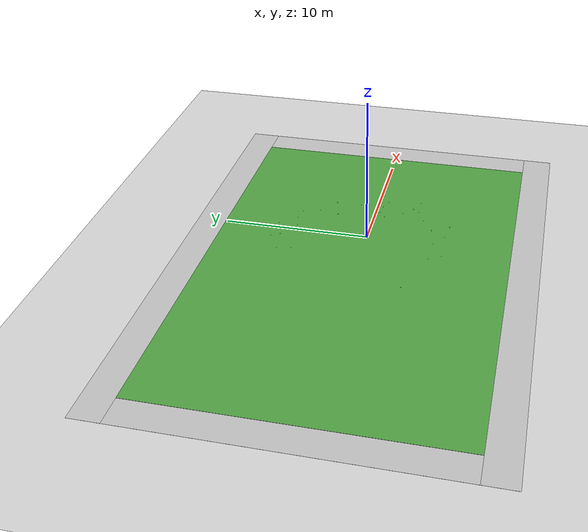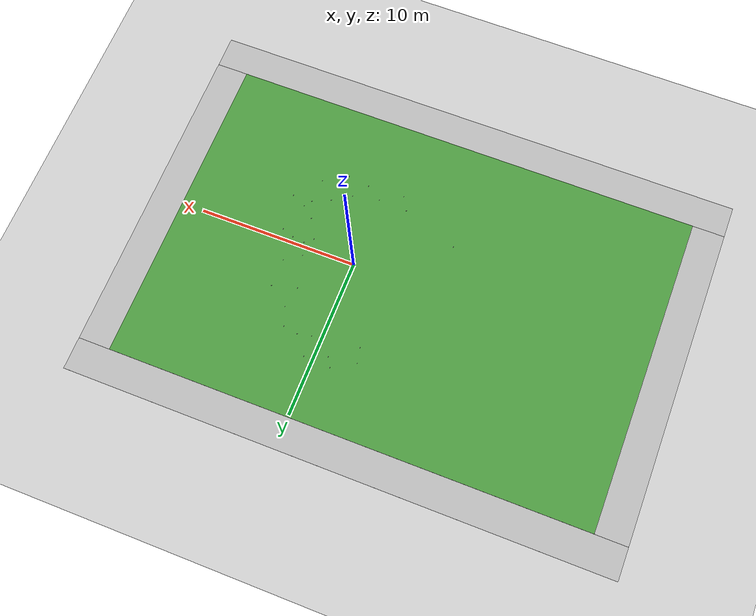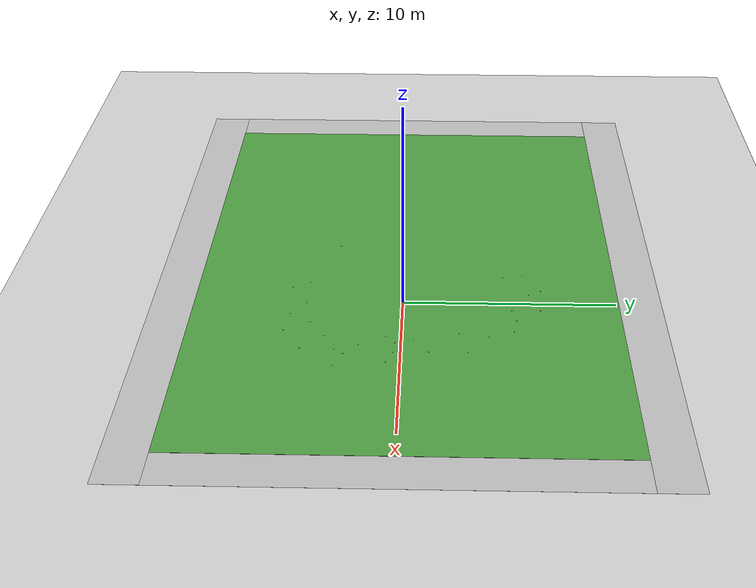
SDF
<sdf version="1.7">
 <world name="default">
  <light name="sun" type="directional">
   <pose>0 0 10 0 -0 0</pose>
   <diffuse>0.8 0.8 0.8 1</diffuse>
   <specular>0.2 0.2 0.2 1</specular>
   <attenuation>
    <range>1000</range>
    <constant>0.9</constant>
    <linear>0.01</linear>
    <quadratic>0.001</quadratic>
   </attenuation>
   <direction>-0.5 0.1 -0.9</direction>
   <spot><inner_angle>0</inner_angle><outer_angle>0</outer_angle><falloff>0</falloff></spot>
  </light>
  <model name="ground_plane">
   <static>1</static>
   <link name="link">
    <collision name="collision">
     <geometry><plane><normal>0 0 1</normal><size>100 100</size></plane></geometry>
     <surface><friction><ode><mu>100</mu><mu2>50</mu2></ode></friction></surface>
    </collision>
    <visual name="visual">
     <cast_shadows>0</cast_shadows>
     <geometry><plane><normal>0 0 1</normal><size>100 100</size></plane></geometry>
     <material>
      <script><uri>file://media/materials/scripts/gazebo.material</uri><name>Gazebo/Grey</name></script>
     </material>
    </visual>
   </link>
  </model>
  <gravity>0 0 -9.8</gravity>
  <magnetic_field>6e-06 2.3e-05 -4.2e-05</magnetic_field>
  <atmosphere type="adiabatic"/>
  <physics type="ode">
   <max_step_size>0.001</max_step_size>
   <real_time_factor>1</real_time_factor>
   <real_time_update_rate>1000</real_time_update_rate>
  </physics>
  <scene><ambient>0.4 0.4 0.4 1</ambient><background>0.7 0.7 0.7 1</background><shadows>1</shadows></scene>
  <audio><device>default</device></audio>
  <spherical_coordinates>
   <surface_model>EARTH_WGS84</surface_model>
   <latitude_deg>0</latitude_deg>
   <longitude_deg>0</longitude_deg>
   <elevation>0</elevation>
   <heading_deg>0</heading_deg>
  </spherical_coordinates>
  <model name="golfball">
   <link name="link_1">
    <inertial>
     <mass>0.0424169</mass>
     <inertia>
      <ixx>1.007e-05</ixx>
      <ixy>0</ixy>
      <ixz>0</ixz>
      <iyy>1.007e-05</iyy>
      <iyz>0</iyz>
      <izz>1.007e-05</izz>
     </inertia>
     <pose>0.024 0 0 0 -0 0</pose>
    </inertial>
    <self_collide>1</self_collide>
    <kinematic>1</kinematic>
    <visual name="visual">
     <geometry><sphere><radius>0.0243658</radius></sphere></geometry>
     <material>
      <lighting>1</lighting>
      <script><uri>file://media/materials/scripts/gazebo.material</uri><name>Gazebo/White</name></script>
      <shader type="pixel"><normal_map>__default__</normal_map></shader>
      <ambient>1 1 1 1</ambient>
      <diffuse>1 1 1 1</diffuse>
      <specular>0 0 0 1</specular>
      <emissive>0 0 0 1</emissive>
     </material>
    </visual>
    <collision name="collision">
     <max_contacts>1</max_contacts>
     <geometry><sphere><radius>0.024366</radius></sphere></geometry>
     <surface>
      <friction>
       <ode><mu>1</mu><mu2>1</mu2><fdir1>0 0 0</fdir1><slip1>0</slip1><slip2>0</slip2></ode>
       <torsional>
        <coefficient>1</coefficient>
        <patch_radius>0</patch_radius>
        <surface_radius>0</surface_radius>
        <use_patch_radius>1</use_patch_radius>
        <ode><slip>0</slip></ode>
       </torsional>
      </friction>
      <bounce><restitution_coefficient>0</restitution_coefficient><threshold>1e+06</threshold></bounce>
      <contact>
       <collide_without_contact>0</collide_without_contact>
       <collide_without_contact_bitmask>1</collide_without_contact_bitmask>
       <collide_bitmask>1</collide_bitmask>
       <ode>
        <soft_cfm>0</soft_cfm>
        <soft_erp>0.2</soft_erp>
        <kp>1e+13</kp>
        <kd>1</kd>
        <max_vel>0.01</max_vel>
        <min_depth>0</min_depth>
       </ode>
       <bullet>
        <split_impulse>1</split_impulse>
        <split_impulse_penetration_threshold>-0.01</split_impulse_penetration_threshold>
        <soft_cfm>0</soft_cfm>
        <soft_erp>0.2</soft_erp>
        <kp>1e+13</kp>
        <kd>1</kd>
       </bullet>
      </contact>
     </surface>
    </collision>
   </link>
   <static>0</static>
   <pose>2.88565 -0.695061 0.026999 0 -0 0</pose>
  </model>
  <model name="robocup_3d_field">
   <static>1</static>
   <link name="field">
    <pose>0 0 0.01 0 -0 0</pose>
    <collision name="collision">
     <geometry><plane><normal>0 0 1</normal><size>30 20</size></plane></geometry>
     <surface><friction><ode><mu>100</mu><mu2>50</mu2></ode></friction></surface>
    </collision>
    <visual name="base1">
     <pose>0 11 0.001 0 -0 0</pose>
     <cast_shadows>0</cast_shadows>
     <geometry><plane><normal>0 0 1</normal><size>34 2</size></plane></geometry>
     <material>
      <script>
       <uri>model://robocup_3Dsim_field/materials/scripts/</uri>
       <uri>model://robocup_3Dsim_field/materials/textures/</uri>
       <name>RoboCup/FieldBorder</name>
      </script>
     </material>
    </visual>
    <visual name="base2">
     <pose>0 -11 0.001 0 -0 0</pose>
     <cast_shadows>0</cast_shadows>
     <geometry><plane><normal>0 0 1</normal><size>34 2</size></plane></geometry>
     <material>
      <script>
       <uri>model://robocup_3Dsim_field/materials/scripts/</uri>
       <uri>model://robocup_3Dsim_field/materials/textures/</uri>
       <name>RoboCup/FieldBorder</name>
      </script>
     </material>
    </visual>
    <visual name="base3">
     <pose>16 0 0.001 0 -0 0</pose>
     <cast_shadows>0</cast_shadows>
     <geometry><plane><normal>0 0 1</normal><size>2 20</size></plane></geometry>
     <material>
      <script>
       <uri>model://robocup_3Dsim_field/materials/scripts/</uri>
       <uri>model://robocup_3Dsim_field/materials/textures/</uri>
       <name>RoboCup/FieldBorder</name>
      </script>
     </material>
    </visual>
    <visual name="base4">
     <pose>-16 0 0.001 0 -0 0</pose>
     <cast_shadows>0</cast_shadows>
     <geometry><plane><normal>0 0 1</normal><size>2 20</size></plane></geometry>
     <material>
      <script>
       <uri>model://robocup_3Dsim_field/materials/scripts/</uri>
       <uri>model://robocup_3Dsim_field/materials/textures/</uri>
       <name>RoboCup/FieldBorder</name>
      </script>
     </material>
    </visual>
    <visual name="carpet">
     <cast_shadows>0</cast_shadows>
     <geometry><plane><normal>0 0 1</normal><size>30 20</size></plane></geometry>
     <material>
      <script>
       <uri>model://robocup_3Dsim_field/materials/scripts/</uri>
       <uri>model://robocup_3Dsim_field/materials/textures/</uri>
       <name>RoboCup/Grass</name>
      </script>
     </material>
    </visual>
   </link>
   <pose>-3.54462 0.142139 0 0 -0 0</pose>
  </model>
  <model name="golfball_clone">
   <link name="link_1">
    <inertial>
     <mass>0.0424169</mass>
     <inertia>
      <ixx>1.007e-05</ixx>
      <ixy>0</ixy>
      <ixz>0</ixz>
      <iyy>1.007e-05</iyy>
      <iyz>0</iyz>
      <izz>1.007e-05</izz>
     </inertia>
     <pose>0.024 0 0 0 -0 0</pose>
    </inertial>
    <self_collide>1</self_collide>
    <kinematic>1</kinematic>
    <visual name="visual">
     <geometry><sphere><radius>0.0243658</radius></sphere></geometry>
     <material>
      <lighting>1</lighting>
      <script><uri>file://media/materials/scripts/gazebo.material</uri><name>Gazebo/White</name></script>
      <shader type="pixel"><normal_map>__default__</normal_map></shader>
      <ambient>1 1 1 1</ambient>
      <diffuse>1 1 1 1</diffuse>
      <specular>0 0 0 1</specular>
      <emissive>0 0 0 1</emissive>
     </material>
    </visual>
    <collision name="collision">
     <max_contacts>1</max_contacts>
     <geometry><sphere><radius>0.024366</radius></sphere></geometry>
     <surface>
      <friction>
       <ode><mu>1</mu><mu2>1</mu2><fdir1>0 0 0</fdir1><slip1>0</slip1><slip2>0</slip2></ode>
       <torsional>
        <coefficient>1</coefficient>
        <patch_radius>0</patch_radius>
        <surface_radius>0</surface_radius>
        <use_patch_radius>1</use_patch_radius>
        <ode><slip>0</slip></ode>
       </torsional>
      </friction>
      <bounce><restitution_coefficient>0</restitution_coefficient><threshold>1e+06</threshold></bounce>
      <contact>
       <collide_without_contact>0</collide_without_contact>
       <collide_without_contact_bitmask>1</collide_without_contact_bitmask>
       <collide_bitmask>1</collide_bitmask>
       <ode>
        <soft_cfm>0</soft_cfm>
        <soft_erp>0.2</soft_erp>
        <kp>1e+13</kp>
        <kd>1</kd>
        <max_vel>0.01</max_vel>
        <min_depth>0</min_depth>
       </ode>
       <bullet>
        <split_impulse>1</split_impulse>
        <split_impulse_penetration_threshold>-0.01</split_impulse_penetration_threshold>
        <soft_cfm>0</soft_cfm>
        <soft_erp>0.2</soft_erp>
        <kp>1e+13</kp>
        <kd>1</kd>
       </bullet>
      </contact>
     </surface>
    </collision>
   </link>
   <static>0</static>
   <pose>3.37922 -0.276184 0.026999 0 -0 0</pose>
  </model>
  <model name="golfball_clone_0">
   <link name="link_1">
    <inertial>
     <mass>0.0424169</mass>
     <inertia>
      <ixx>1.007e-05</ixx>
      <ixy>0</ixy>
      <ixz>0</ixz>
      <iyy>1.007e-05</iyy>
      <iyz>0</iyz>
      <izz>1.007e-05</izz>
     </inertia>
     <pose>0.024 0 0 0 -0 0</pose>
    </inertial>
    <self_collide>1</self_collide>
    <kinematic>1</kinematic>
    <visual name="visual">
     <geometry><sphere><radius>0.0243658</radius></sphere></geometry>
     <material>
      <lighting>1</lighting>
      <script><uri>file://media/materials/scripts/gazebo.material</uri><name>Gazebo/White</name></script>
      <shader type="pixel"><normal_map>__default__</normal_map></shader>
      <ambient>1 1 1 1</ambient>
      <diffuse>1 1 1 1</diffuse>
      <specular>0 0 0 1</specular>
      <emissive>0 0 0 1</emissive>
     </material>
    </visual>
    <collision name="collision">
     <max_contacts>1</max_contacts>
     <geometry><sphere><radius>0.024366</radius></sphere></geometry>
     <surface>
      <friction>
       <ode><mu>1</mu><mu2>1</mu2><fdir1>0 0 0</fdir1><slip1>0</slip1><slip2>0</slip2></ode>
       <torsional>
        <coefficient>1</coefficient>
        <patch_radius>0</patch_radius>
        <surface_radius>0</surface_radius>
        <use_patch_radius>1</use_patch_radius>
        <ode><slip>0</slip></ode>
       </torsional>
      </friction>
      <bounce><restitution_coefficient>0</restitution_coefficient><threshold>1e+06</threshold></bounce>
      <contact>
       <collide_without_contact>0</collide_without_contact>
       <collide_without_contact_bitmask>1</collide_without_contact_bitmask>
       <collide_bitmask>1</collide_bitmask>
       <ode>
        <soft_cfm>0</soft_cfm>
        <soft_erp>0.2</soft_erp>
        <kp>1e+13</kp>
        <kd>1</kd>
        <max_vel>0.01</max_vel>
        <min_depth>0</min_depth>
       </ode>
       <bullet>
        <split_impulse>1</split_impulse>
        <split_impulse_penetration_threshold>-0.01</split_impulse_penetration_threshold>
        <soft_cfm>0</soft_cfm>
        <soft_erp>0.2</soft_erp>
        <kp>1e+13</kp>
        <kd>1</kd>
       </bullet>
      </contact>
     </surface>
    </collision>
   </link>
   <static>0</static>
   <pose>3.11756 0.554738 0.026999 0 -0 0</pose>
  </model>
  <model name="golfball_clone_1">
   <link name="link_1">
    <inertial>
     <mass>0.0424169</mass>
     <inertia>
      <ixx>1.007e-05</ixx>
      <ixy>0</ixy>
      <ixz>0</ixz>
      <iyy>1.007e-05</iyy>
      <iyz>0</iyz>
      <izz>1.007e-05</izz>
     </inertia>
     <pose>0.024 0 0 0 -0 0</pose>
    </inertial>
    <self_collide>1</self_collide>
    <kinematic>1</kinematic>
    <visual name="visual">
     <geometry><sphere><radius>0.0243658</radius></sphere></geometry>
     <material>
      <lighting>1</lighting>
      <script><uri>file://media/materials/scripts/gazebo.material</uri><name>Gazebo/White</name></script>
      <shader type="pixel"><normal_map>__default__</normal_map></shader>
      <ambient>1 1 1 1</ambient>
      <diffuse>1 1 1 1</diffuse>
      <specular>0 0 0 1</specular>
      <emissive>0 0 0 1</emissive>
     </material>
    </visual>
    <collision name="collision">
     <max_contacts>1</max_contacts>
     <geometry><sphere><radius>0.024366</radius></sphere></geometry>
     <surface>
      <friction>
       <ode><mu>1</mu><mu2>1</mu2><fdir1>0 0 0</fdir1><slip1>0</slip1><slip2>0</slip2></ode>
       <torsional>
        <coefficient>1</coefficient>
        <patch_radius>0</patch_radius>
        <surface_radius>0</surface_radius>
        <use_patch_radius>1</use_patch_radius>
        <ode><slip>0</slip></ode>
       </torsional>
      </friction>
      <bounce><restitution_coefficient>0</restitution_coefficient><threshold>1e+06</threshold></bounce>
      <contact>
       <collide_without_contact>0</collide_without_contact>
       <collide_without_contact_bitmask>1</collide_without_contact_bitmask>
       <collide_bitmask>1</collide_bitmask>
       <ode>
        <soft_cfm>0</soft_cfm>
        <soft_erp>0.2</soft_erp>
        <kp>1e+13</kp>
        <kd>1</kd>
        <max_vel>0.01</max_vel>
        <min_depth>0</min_depth>
       </ode>
       <bullet>
        <split_impulse>1</split_impulse>
        <split_impulse_penetration_threshold>-0.01</split_impulse_penetration_threshold>
        <soft_cfm>0</soft_cfm>
        <soft_erp>0.2</soft_erp>
        <kp>1e+13</kp>
        <kd>1</kd>
       </bullet>
      </contact>
     </surface>
    </collision>
   </link>
   <static>0</static>
   <pose>3.581 -1.91333 0.026999 0 -0 0</pose>
  </model>
  <model name="golfball_clone_2">
   <link name="link_1">
    <inertial>
     <mass>0.0424169</mass>
     <inertia>
      <ixx>1.007e-05</ixx>
      <ixy>0</ixy>
      <ixz>0</ixz>
      <iyy>1.007e-05</iyy>
      <iyz>0</iyz>
      <izz>1.007e-05</izz>
     </inertia>
     <pose>0.024 0 0 0 -0 0</pose>
    </inertial>
    <self_collide>1</self_collide>
    <kinematic>1</kinematic>
    <visual name="visual">
     <geometry><sphere><radius>0.0243658</radius></sphere></geometry>
     <material>
      <lighting>1</lighting>
      <script><uri>file://media/materials/scripts/gazebo.material</uri><name>Gazebo/White</name></script>
      <shader type="pixel"><normal_map>__default__</normal_map></shader>
      <ambient>1 1 1 1</ambient>
      <diffuse>1 1 1 1</diffuse>
      <specular>0 0 0 1</specular>
      <emissive>0 0 0 1</emissive>
     </material>
    </visual>
    <collision name="collision">
     <max_contacts>1</max_contacts>
     <geometry><sphere><radius>0.024366</radius></sphere></geometry>
     <surface>
      <friction>
       <ode><mu>1</mu><mu2>1</mu2><fdir1>0 0 0</fdir1><slip1>0</slip1><slip2>0</slip2></ode>
       <torsional>
        <coefficient>1</coefficient>
        <patch_radius>0</patch_radius>
        <surface_radius>0</surface_radius>
        <use_patch_radius>1</use_patch_radius>
        <ode><slip>0</slip></ode>
       </torsional>
      </friction>
      <bounce><restitution_coefficient>0</restitution_coefficient><threshold>1e+06</threshold></bounce>
      <contact>
       <collide_without_contact>0</collide_without_contact>
       <collide_without_contact_bitmask>1</collide_without_contact_bitmask>
       <collide_bitmask>1</collide_bitmask>
       <ode>
        <soft_cfm>0</soft_cfm>
        <soft_erp>0.2</soft_erp>
        <kp>1e+13</kp>
        <kd>1</kd>
        <max_vel>0.01</max_vel>
        <min_depth>0</min_depth>
       </ode>
       <bullet>
        <split_impulse>1</split_impulse>
        <split_impulse_penetration_threshold>-0.01</split_impulse_penetration_threshold>
        <soft_cfm>0</soft_cfm>
        <soft_erp>0.2</soft_erp>
        <kp>1e+13</kp>
        <kd>1</kd>
       </bullet>
      </contact>
     </surface>
    </collision>
   </link>
   <static>0</static>
   <pose>4.11207 1.24897 0.026999 0 -0 0</pose>
  </model>
  <model name="golfball_clone_3">
   <link name="link_1">
    <inertial>
     <mass>0.0424169</mass>
     <inertia>
      <ixx>1.007e-05</ixx>
      <ixy>0</ixy>
      <ixz>0</ixz>
      <iyy>1.007e-05</iyy>
      <iyz>0</iyz>
      <izz>1.007e-05</izz>
     </inertia>
     <pose>0.024 0 0 0 -0 0</pose>
    </inertial>
    <self_collide>1</self_collide>
    <kinematic>1</kinematic>
    <visual name="visual">
     <geometry><sphere><radius>0.0243658</radius></sphere></geometry>
     <material>
      <lighting>1</lighting>
      <script><uri>file://media/materials/scripts/gazebo.material</uri><name>Gazebo/White</name></script>
      <shader type="pixel"><normal_map>__default__</normal_map></shader>
      <ambient>1 1 1 1</ambient>
      <diffuse>1 1 1 1</diffuse>
      <specular>0 0 0 1</specular>
      <emissive>0 0 0 1</emissive>
     </material>
    </visual>
    <collision name="collision">
     <max_contacts>1</max_contacts>
     <geometry><sphere><radius>0.024366</radius></sphere></geometry>
     <surface>
      <friction>
       <ode><mu>1</mu><mu2>1</mu2><fdir1>0 0 0</fdir1><slip1>0</slip1><slip2>0</slip2></ode>
       <torsional>
        <coefficient>1</coefficient>
        <patch_radius>0</patch_radius>
        <surface_radius>0</surface_radius>
        <use_patch_radius>1</use_patch_radius>
        <ode><slip>0</slip></ode>
       </torsional>
      </friction>
      <bounce><restitution_coefficient>0</restitution_coefficient><threshold>1e+06</threshold></bounce>
      <contact>
       <collide_without_contact>0</collide_without_contact>
       <collide_without_contact_bitmask>1</collide_without_contact_bitmask>
       <collide_bitmask>1</collide_bitmask>
       <ode>
        <soft_cfm>0</soft_cfm>
        <soft_erp>0.2</soft_erp>
        <kp>1e+13</kp>
        <kd>1</kd>
        <max_vel>0.01</max_vel>
        <min_depth>0</min_depth>
       </ode>
       <bullet>
        <split_impulse>1</split_impulse>
        <split_impulse_penetration_threshold>-0.01</split_impulse_penetration_threshold>
        <soft_cfm>0</soft_cfm>
        <soft_erp>0.2</soft_erp>
        <kp>1e+13</kp>
        <kd>1</kd>
       </bullet>
      </contact>
     </surface>
    </collision>
   </link>
   <static>0</static>
   <pose>2.8186 3.97255 0.026999 0 -0 0</pose>
  </model>
  <model name="golfball_clone_4">
   <link name="link_1">
    <inertial>
     <mass>0.0424169</mass>
     <inertia>
      <ixx>1.007e-05</ixx>
      <ixy>0</ixy>
      <ixz>0</ixz>
      <iyy>1.007e-05</iyy>
      <iyz>0</iyz>
      <izz>1.007e-05</izz>
     </inertia>
     <pose>0.024 0 0 0 -0 0</pose>
    </inertial>
    <self_collide>1</self_collide>
    <kinematic>1</kinematic>
    <visual name="visual">
     <geometry><sphere><radius>0.0243658</radius></sphere></geometry>
     <material>
      <lighting>1</lighting>
      <script><uri>file://media/materials/scripts/gazebo.material</uri><name>Gazebo/White</name></script>
      <shader type="pixel"><normal_map>__default__</normal_map></shader>
      <ambient>1 1 1 1</ambient>
      <diffuse>1 1 1 1</diffuse>
      <specular>0 0 0 1</specular>
      <emissive>0 0 0 1</emissive>
     </material>
    </visual>
    <collision name="collision">
     <max_contacts>1</max_contacts>
     <geometry><sphere><radius>0.024366</radius></sphere></geometry>
     <surface>
      <friction>
       <ode><mu>1</mu><mu2>1</mu2><fdir1>0 0 0</fdir1><slip1>0</slip1><slip2>0</slip2></ode>
       <torsional>
        <coefficient>1</coefficient>
        <patch_radius>0</patch_radius>
        <surface_radius>0</surface_radius>
        <use_patch_radius>1</use_patch_radius>
        <ode><slip>0</slip></ode>
       </torsional>
      </friction>
      <bounce><restitution_coefficient>0</restitution_coefficient><threshold>1e+06</threshold></bounce>
      <contact>
       <collide_without_contact>0</collide_without_contact>
       <collide_without_contact_bitmask>1</collide_without_contact_bitmask>
       <collide_bitmask>1</collide_bitmask>
       <ode>
        <soft_cfm>0</soft_cfm>
        <soft_erp>0.2</soft_erp>
        <kp>1e+13</kp>
        <kd>1</kd>
        <max_vel>0.01</max_vel>
        <min_depth>0</min_depth>
       </ode>
       <bullet>
        <split_impulse>1</split_impulse>
        <split_impulse_penetration_threshold>-0.01</split_impulse_penetration_threshold>
        <soft_cfm>0</soft_cfm>
        <soft_erp>0.2</soft_erp>
        <kp>1e+13</kp>
        <kd>1</kd>
       </bullet>
      </contact>
     </surface>
    </collision>
   </link>
   <static>0</static>
   <pose>5.2335 -2.95911 0.026999 0 -0 0</pose>
  </model>
  <model name="golfball_clone_5">
   <link name="link_1">
    <inertial>
     <mass>0.0424169</mass>
     <inertia>
      <ixx>1.007e-05</ixx>
      <ixy>0</ixy>
      <ixz>0</ixz>
      <iyy>1.007e-05</iyy>
      <iyz>0</iyz>
      <izz>1.007e-05</izz>
     </inertia>
     <pose>0.024 0 0 0 -0 0</pose>
    </inertial>
    <self_collide>1</self_collide>
    <kinematic>1</kinematic>
    <visual name="visual">
     <geometry><sphere><radius>0.0243658</radius></sphere></geometry>
     <material>
      <lighting>1</lighting>
      <script><uri>file://media/materials/scripts/gazebo.material</uri><name>Gazebo/White</name></script>
      <shader type="pixel"><normal_map>__default__</normal_map></shader>
      <ambient>1 1 1 1</ambient>
      <diffuse>1 1 1 1</diffuse>
      <specular>0 0 0 1</specular>
      <emissive>0 0 0 1</emissive>
     </material>
    </visual>
    <collision name="collision">
     <max_contacts>1</max_contacts>
     <geometry><sphere><radius>0.024366</radius></sphere></geometry>
     <surface>
      <friction>
       <ode><mu>1</mu><mu2>1</mu2><fdir1>0 0 0</fdir1><slip1>0</slip1><slip2>0</slip2></ode>
       <torsional>
        <coefficient>1</coefficient>
        <patch_radius>0</patch_radius>
        <surface_radius>0</surface_radius>
        <use_patch_radius>1</use_patch_radius>
        <ode><slip>0</slip></ode>
       </torsional>
      </friction>
      <bounce><restitution_coefficient>0</restitution_coefficient><threshold>1e+06</threshold></bounce>
      <contact>
       <collide_without_contact>0</collide_without_contact>
       <collide_without_contact_bitmask>1</collide_without_contact_bitmask>
       <collide_bitmask>1</collide_bitmask>
       <ode>
        <soft_cfm>0</soft_cfm>
        <soft_erp>0.2</soft_erp>
        <kp>1e+13</kp>
        <kd>1</kd>
        <max_vel>0.01</max_vel>
        <min_depth>0</min_depth>
       </ode>
       <bullet>
        <split_impulse>1</split_impulse>
        <split_impulse_penetration_threshold>-0.01</split_impulse_penetration_threshold>
        <soft_cfm>0</soft_cfm>
        <soft_erp>0.2</soft_erp>
        <kp>1e+13</kp>
        <kd>1</kd>
       </bullet>
      </contact>
     </surface>
    </collision>
   </link>
   <static>0</static>
   <pose>1.77343 -4.22297 0.026999 0 -0 0</pose>
  </model>
  <model name="golfball_clone_6">
   <link name="link_1">
    <inertial>
     <mass>0.0424169</mass>
     <inertia>
      <ixx>1.007e-05</ixx>
      <ixy>0</ixy>
      <ixz>0</ixz>
      <iyy>1.007e-05</iyy>
      <iyz>0</iyz>
      <izz>1.007e-05</izz>
     </inertia>
     <pose>0.024 0 0 0 -0 0</pose>
    </inertial>
    <self_collide>1</self_collide>
    <kinematic>1</kinematic>
    <visual name="visual">
     <geometry><sphere><radius>0.0243658</radius></sphere></geometry>
     <material>
      <lighting>1</lighting>
      <script><uri>file://media/materials/scripts/gazebo.material</uri><name>Gazebo/White</name></script>
      <shader type="pixel"><normal_map>__default__</normal_map></shader>
      <ambient>1 1 1 1</ambient>
      <diffuse>1 1 1 1</diffuse>
      <specular>0 0 0 1</specular>
      <emissive>0 0 0 1</emissive>
     </material>
    </visual>
    <collision name="collision">
     <max_contacts>1</max_contacts>
     <geometry><sphere><radius>0.024366</radius></sphere></geometry>
     <surface>
      <friction>
       <ode><mu>1</mu><mu2>1</mu2><fdir1>0 0 0</fdir1><slip1>0</slip1><slip2>0</slip2></ode>
       <torsional>
        <coefficient>1</coefficient>
        <patch_radius>0</patch_radius>
        <surface_radius>0</surface_radius>
        <use_patch_radius>1</use_patch_radius>
        <ode><slip>0</slip></ode>
       </torsional>
      </friction>
      <bounce><restitution_coefficient>0</restitution_coefficient><threshold>1e+06</threshold></bounce>
      <contact>
       <collide_without_contact>0</collide_without_contact>
       <collide_without_contact_bitmask>1</collide_without_contact_bitmask>
       <collide_bitmask>1</collide_bitmask>
       <ode>
        <soft_cfm>0</soft_cfm>
        <soft_erp>0.2</soft_erp>
        <kp>1e+13</kp>
        <kd>1</kd>
        <max_vel>0.01</max_vel>
        <min_depth>0</min_depth>
       </ode>
       <bullet>
        <split_impulse>1</split_impulse>
        <split_impulse_penetration_threshold>-0.01</split_impulse_penetration_threshold>
        <soft_cfm>0</soft_cfm>
        <soft_erp>0.2</soft_erp>
        <kp>1e+13</kp>
        <kd>1</kd>
       </bullet>
      </contact>
     </surface>
    </collision>
   </link>
   <static>0</static>
   <pose>0.122762 -4.54773 0.026999 0 -0 0</pose>
  </model>
  <model name="golfball_clone_7">
   <link name="link_1">
    <inertial>
     <mass>0.0424169</mass>
     <inertia>
      <ixx>1.007e-05</ixx>
      <ixy>0</ixy>
      <ixz>0</ixz>
      <iyy>1.007e-05</iyy>
      <iyz>0</iyz>
      <izz>1.007e-05</izz>
     </inertia>
     <pose>0.024 0 0 0 -0 0</pose>
    </inertial>
    <self_collide>1</self_collide>
    <kinematic>1</kinematic>
    <visual name="visual">
     <geometry><sphere><radius>0.0243658</radius></sphere></geometry>
     <material>
      <lighting>1</lighting>
      <script><uri>file://media/materials/scripts/gazebo.material</uri><name>Gazebo/White</name></script>
      <shader type="pixel"><normal_map>__default__</normal_map></shader>
      <ambient>1 1 1 1</ambient>
      <diffuse>1 1 1 1</diffuse>
      <specular>0 0 0 1</specular>
      <emissive>0 0 0 1</emissive>
     </material>
    </visual>
    <collision name="collision">
     <max_contacts>1</max_contacts>
     <geometry><sphere><radius>0.024366</radius></sphere></geometry>
     <surface>
      <friction>
       <ode><mu>1</mu><mu2>1</mu2><fdir1>0 0 0</fdir1><slip1>0</slip1><slip2>0</slip2></ode>
       <torsional>
        <coefficient>1</coefficient>
        <patch_radius>0</patch_radius>
        <surface_radius>0</surface_radius>
        <use_patch_radius>1</use_patch_radius>
        <ode><slip>0</slip></ode>
       </torsional>
      </friction>
      <bounce><restitution_coefficient>0</restitution_coefficient><threshold>1e+06</threshold></bounce>
      <contact>
       <collide_without_contact>0</collide_without_contact>
       <collide_without_contact_bitmask>1</collide_without_contact_bitmask>
       <collide_bitmask>1</collide_bitmask>
       <ode>
        <soft_cfm>0</soft_cfm>
        <soft_erp>0.2</soft_erp>
        <kp>1e+13</kp>
        <kd>1</kd>
        <max_vel>0.01</max_vel>
        <min_depth>0</min_depth>
       </ode>
       <bullet>
        <split_impulse>1</split_impulse>
        <split_impulse_penetration_threshold>-0.01</split_impulse_penetration_threshold>
        <soft_cfm>0</soft_cfm>
        <soft_erp>0.2</soft_erp>
        <kp>1e+13</kp>
        <kd>1</kd>
       </bullet>
      </contact>
     </surface>
    </collision>
   </link>
   <static>0</static>
   <pose>3.93282 -4.53007 0.026999 0 -0 0</pose>
  </model>
  <model name="golfball_clone_8">
   <link name="link_1">
    <inertial>
     <mass>0.0424169</mass>
     <inertia>
      <ixx>1.007e-05</ixx>
      <ixy>0</ixy>
      <ixz>0</ixz>
      <iyy>1.007e-05</iyy>
      <iyz>0</iyz>
      <izz>1.007e-05</izz>
     </inertia>
     <pose>0.024 0 0 0 -0 0</pose>
    </inertial>
    <self_collide>1</self_collide>
    <kinematic>1</kinematic>
    <visual name="visual">
     <geometry><sphere><radius>0.0243658</radius></sphere></geometry>
     <material>
      <lighting>1</lighting>
      <script><uri>file://media/materials/scripts/gazebo.material</uri><name>Gazebo/White</name></script>
      <shader type="pixel"><normal_map>__default__</normal_map></shader>
      <ambient>1 1 1 1</ambient>
      <diffuse>1 1 1 1</diffuse>
      <specular>0 0 0 1</specular>
      <emissive>0 0 0 1</emissive>
     </material>
    </visual>
    <collision name="collision">
     <max_contacts>1</max_contacts>
     <geometry><sphere><radius>0.024366</radius></sphere></geometry>
     <surface>
      <friction>
       <ode><mu>1</mu><mu2>1</mu2><fdir1>0 0 0</fdir1><slip1>0</slip1><slip2>0</slip2></ode>
       <torsional>
        <coefficient>1</coefficient>
        <patch_radius>0</patch_radius>
        <surface_radius>0</surface_radius>
        <use_patch_radius>1</use_patch_radius>
        <ode><slip>0</slip></ode>
       </torsional>
      </friction>
      <bounce><restitution_coefficient>0</restitution_coefficient><threshold>1e+06</threshold></bounce>
      <contact>
       <collide_without_contact>0</collide_without_contact>
       <collide_without_contact_bitmask>1</collide_without_contact_bitmask>
       <collide_bitmask>1</collide_bitmask>
       <ode>
        <soft_cfm>0</soft_cfm>
        <soft_erp>0.2</soft_erp>
        <kp>1e+13</kp>
        <kd>1</kd>
        <max_vel>0.01</max_vel>
        <min_depth>0</min_depth>
       </ode>
       <bullet>
        <split_impulse>1</split_impulse>
        <split_impulse_penetration_threshold>-0.01</split_impulse_penetration_threshold>
        <soft_cfm>0</soft_cfm>
        <soft_erp>0.2</soft_erp>
        <kp>1e+13</kp>
        <kd>1</kd>
       </bullet>
      </contact>
     </surface>
    </collision>
   </link>
   <static>0</static>
   <pose>4.92055 -0.645184 0.026999 0 -0 0</pose>
  </model>
  <model name="golfball_clone_9">
   <link name="link_1">
    <inertial>
     <mass>0.0424169</mass>
     <inertia>
      <ixx>1.007e-05</ixx>
      <ixy>0</ixy>
      <ixz>0</ixz>
      <iyy>1.007e-05</iyy>
      <iyz>0</iyz>
      <izz>1.007e-05</izz>
     </inertia>
     <pose>0.024 0 0 0 -0 0</pose>
    </inertial>
    <self_collide>1</self_collide>
    <kinematic>1</kinematic>
    <visual name="visual">
     <geometry><sphere><radius>0.0243658</radius></sphere></geometry>
     <material>
      <lighting>1</lighting>
      <script><uri>file://media/materials/scripts/gazebo.material</uri><name>Gazebo/White</name></script>
      <shader type="pixel"><normal_map>__default__</normal_map></shader>
      <ambient>1 1 1 1</ambient>
      <diffuse>1 1 1 1</diffuse>
      <specular>0 0 0 1</specular>
      <emissive>0 0 0 1</emissive>
     </material>
    </visual>
    <collision name="collision">
     <max_contacts>1</max_contacts>
     <geometry><sphere><radius>0.024366</radius></sphere></geometry>
     <surface>
      <friction>
       <ode><mu>1</mu><mu2>1</mu2><fdir1>0 0 0</fdir1><slip1>0</slip1><slip2>0</slip2></ode>
       <torsional>
        <coefficient>1</coefficient>
        <patch_radius>0</patch_radius>
        <surface_radius>0</surface_radius>
        <use_patch_radius>1</use_patch_radius>
        <ode><slip>0</slip></ode>
       </torsional>
      </friction>
      <bounce><restitution_coefficient>0</restitution_coefficient><threshold>1e+06</threshold></bounce>
      <contact>
       <collide_without_contact>0</collide_without_contact>
       <collide_without_contact_bitmask>1</collide_without_contact_bitmask>
       <collide_bitmask>1</collide_bitmask>
       <ode>
        <soft_cfm>0</soft_cfm>
        <soft_erp>0.2</soft_erp>
        <kp>1e+13</kp>
        <kd>1</kd>
        <max_vel>0.01</max_vel>
        <min_depth>0</min_depth>
       </ode>
       <bullet>
        <split_impulse>1</split_impulse>
        <split_impulse_penetration_threshold>-0.01</split_impulse_penetration_threshold>
        <soft_cfm>0</soft_cfm>
        <soft_erp>0.2</soft_erp>
        <kp>1e+13</kp>
        <kd>1</kd>
       </bullet>
      </contact>
     </surface>
    </collision>
   </link>
   <static>0</static>
   <pose>4.11938 3.00921 0.026999 0 -0 0</pose>
  </model>
  <model name="golfball_clone_10">
   <link name="link_1">
    <inertial>
     <mass>0.0424169</mass>
     <inertia>
      <ixx>1.007e-05</ixx>
      <ixy>0</ixy>
      <ixz>0</ixz>
      <iyy>1.007e-05</iyy>
      <iyz>0</iyz>
      <izz>1.007e-05</izz>
     </inertia>
     <pose>0.024 0 0 0 -0 0</pose>
    </inertial>
    <self_collide>1</self_collide>
    <kinematic>1</kinematic>
    <visual name="visual">
     <geometry><sphere><radius>0.0243658</radius></sphere></geometry>
     <material>
      <lighting>1</lighting>
      <script><uri>file://media/materials/scripts/gazebo.material</uri><name>Gazebo/White</name></script>
      <shader type="pixel"><normal_map>__default__</normal_map></shader>
      <ambient>1 1 1 1</ambient>
      <diffuse>1 1 1 1</diffuse>
      <specular>0 0 0 1</specular>
      <emissive>0 0 0 1</emissive>
     </material>
    </visual>
    <collision name="collision">
     <max_contacts>1</max_contacts>
     <geometry><sphere><radius>0.024366</radius></sphere></geometry>
     <surface>
      <friction>
       <ode><mu>1</mu><mu2>1</mu2><fdir1>0 0 0</fdir1><slip1>0</slip1><slip2>0</slip2></ode>
       <torsional>
        <coefficient>1</coefficient>
        <patch_radius>0</patch_radius>
        <surface_radius>0</surface_radius>
        <use_patch_radius>1</use_patch_radius>
        <ode><slip>0</slip></ode>
       </torsional>
      </friction>
      <bounce><restitution_coefficient>0</restitution_coefficient><threshold>1e+06</threshold></bounce>
      <contact>
       <collide_without_contact>0</collide_without_contact>
       <collide_without_contact_bitmask>1</collide_without_contact_bitmask>
       <collide_bitmask>1</collide_bitmask>
       <ode>
        <soft_cfm>0</soft_cfm>
        <soft_erp>0.2</soft_erp>
        <kp>1e+13</kp>
        <kd>1</kd>
        <max_vel>0.01</max_vel>
        <min_depth>0</min_depth>
       </ode>
       <bullet>
        <split_impulse>1</split_impulse>
        <split_impulse_penetration_threshold>-0.01</split_impulse_penetration_threshold>
        <soft_cfm>0</soft_cfm>
        <soft_erp>0.2</soft_erp>
        <kp>1e+13</kp>
        <kd>1</kd>
       </bullet>
      </contact>
     </surface>
    </collision>
   </link>
   <static>0</static>
   <pose>2.58674 2.61119 0.026999 0 -0 0</pose>
  </model>
  <model name="golfball_clone_11">
   <link name="link_1">
    <inertial>
     <mass>0.0424169</mass>
     <inertia>
      <ixx>1.007e-05</ixx>
      <ixy>0</ixy>
      <ixz>0</ixz>
      <iyy>1.007e-05</iyy>
      <iyz>0</iyz>
      <izz>1.007e-05</izz>
     </inertia>
     <pose>0.024 0 0 0 -0 0</pose>
    </inertial>
    <self_collide>1</self_collide>
    <kinematic>1</kinematic>
    <visual name="visual">
     <geometry><sphere><radius>0.0243658</radius></sphere></geometry>
     <material>
      <lighting>1</lighting>
      <script><uri>file://media/materials/scripts/gazebo.material</uri><name>Gazebo/White</name></script>
      <shader type="pixel"><normal_map>__default__</normal_map></shader>
      <ambient>1 1 1 1</ambient>
      <diffuse>1 1 1 1</diffuse>
      <specular>0 0 0 1</specular>
      <emissive>0 0 0 1</emissive>
     </material>
    </visual>
    <collision name="collision">
     <max_contacts>1</max_contacts>
     <geometry><sphere><radius>0.024366</radius></sphere></geometry>
     <surface>
      <friction>
       <ode><mu>1</mu><mu2>1</mu2><fdir1>0 0 0</fdir1><slip1>0</slip1><slip2>0</slip2></ode>
       <torsional>
        <coefficient>1</coefficient>
        <patch_radius>0</patch_radius>
        <surface_radius>0</surface_radius>
        <use_patch_radius>1</use_patch_radius>
        <ode><slip>0</slip></ode>
       </torsional>
      </friction>
      <bounce><restitution_coefficient>0</restitution_coefficient><threshold>1e+06</threshold></bounce>
      <contact>
       <collide_without_contact>0</collide_without_contact>
       <collide_without_contact_bitmask>1</collide_without_contact_bitmask>
       <collide_bitmask>1</collide_bitmask>
       <ode>
        <soft_cfm>0</soft_cfm>
        <soft_erp>0.2</soft_erp>
        <kp>1e+13</kp>
        <kd>1</kd>
        <max_vel>0.01</max_vel>
        <min_depth>0</min_depth>
       </ode>
       <bullet>
        <split_impulse>1</split_impulse>
        <split_impulse_penetration_threshold>-0.01</split_impulse_penetration_threshold>
        <soft_cfm>0</soft_cfm>
        <soft_erp>0.2</soft_erp>
        <kp>1e+13</kp>
        <kd>1</kd>
       </bullet>
      </contact>
     </surface>
    </collision>
   </link>
   <static>0</static>
   <pose>0.577654 6.43091 0.026999 0 -0 0</pose>
  </model>
  <model name="golfball_clone_12">
   <link name="link_1">
    <inertial>
     <mass>0.0424169</mass>
     <inertia>
      <ixx>1.007e-05</ixx>
      <ixy>0</ixy>
      <ixz>0</ixz>
      <iyy>1.007e-05</iyy>
      <iyz>0</iyz>
      <izz>1.007e-05</izz>
     </inertia>
     <pose>0.024 0 0 0 -0 0</pose>
    </inertial>
    <self_collide>1</self_collide>
    <kinematic>1</kinematic>
    <visual name="visual">
     <geometry><sphere><radius>0.0243658</radius></sphere></geometry>
     <material>
      <lighting>1</lighting>
      <script><uri>file://media/materials/scripts/gazebo.material</uri><name>Gazebo/White</name></script>
      <shader type="pixel"><normal_map>__default__</normal_map></shader>
      <ambient>1 1 1 1</ambient>
      <diffuse>1 1 1 1</diffuse>
      <specular>0 0 0 1</specular>
      <emissive>0 0 0 1</emissive>
     </material>
    </visual>
    <collision name="collision">
     <max_contacts>1</max_contacts>
     <geometry><sphere><radius>0.024366</radius></sphere></geometry>
     <surface>
      <friction>
       <ode><mu>1</mu><mu2>1</mu2><fdir1>0 0 0</fdir1><slip1>0</slip1><slip2>0</slip2></ode>
       <torsional>
        <coefficient>1</coefficient>
        <patch_radius>0</patch_radius>
        <surface_radius>0</surface_radius>
        <use_patch_radius>1</use_patch_radius>
        <ode><slip>0</slip></ode>
       </torsional>
      </friction>
      <bounce><restitution_coefficient>0</restitution_coefficient><threshold>1e+06</threshold></bounce>
      <contact>
       <collide_without_contact>0</collide_without_contact>
       <collide_without_contact_bitmask>1</collide_without_contact_bitmask>
       <collide_bitmask>1</collide_bitmask>
       <ode>
        <soft_cfm>0</soft_cfm>
        <soft_erp>0.2</soft_erp>
        <kp>1e+13</kp>
        <kd>1</kd>
        <max_vel>0.01</max_vel>
        <min_depth>0</min_depth>
       </ode>
       <bullet>
        <split_impulse>1</split_impulse>
        <split_impulse_penetration_threshold>-0.01</split_impulse_penetration_threshold>
        <soft_cfm>0</soft_cfm>
        <soft_erp>0.2</soft_erp>
        <kp>1e+13</kp>
        <kd>1</kd>
       </bullet>
      </contact>
     </surface>
    </collision>
   </link>
   <static>0</static>
   <pose>-2.52922 5.70734 0.026999 0 -0 0</pose>
  </model>
  <model name="golfball_clone_13">
   <link name="link_1">
    <inertial>
     <mass>0.0424169</mass>
     <inertia>
      <ixx>1.007e-05</ixx>
      <ixy>0</ixy>
      <ixz>0</ixz>
      <iyy>1.007e-05</iyy>
      <iyz>0</iyz>
      <izz>1.007e-05</izz>
     </inertia>
     <pose>0.024 0 0 0 -0 0</pose>
    </inertial>
    <self_collide>1</self_collide>
    <kinematic>1</kinematic>
    <visual name="visual">
     <geometry><sphere><radius>0.0243658</radius></sphere></geometry>
     <material>
      <lighting>1</lighting>
      <script><uri>file://media/materials/scripts/gazebo.material</uri><name>Gazebo/White</name></script>
      <shader type="pixel"><normal_map>__default__</normal_map></shader>
      <ambient>1 1 1 1</ambient>
      <diffuse>1 1 1 1</diffuse>
      <specular>0 0 0 1</specular>
      <emissive>0 0 0 1</emissive>
     </material>
    </visual>
    <collision name="collision">
     <max_contacts>1</max_contacts>
     <geometry><sphere><radius>0.024366</radius></sphere></geometry>
     <surface>
      <friction>
       <ode><mu>1</mu><mu2>1</mu2><fdir1>0 0 0</fdir1><slip1>0</slip1><slip2>0</slip2></ode>
       <torsional>
        <coefficient>1</coefficient>
        <patch_radius>0</patch_radius>
        <surface_radius>0</surface_radius>
        <use_patch_radius>1</use_patch_radius>
        <ode><slip>0</slip></ode>
       </torsional>
      </friction>
      <bounce><restitution_coefficient>0</restitution_coefficient><threshold>1e+06</threshold></bounce>
      <contact>
       <collide_without_contact>0</collide_without_contact>
       <collide_without_contact_bitmask>1</collide_without_contact_bitmask>
       <collide_bitmask>1</collide_bitmask>
       <ode>
        <soft_cfm>0</soft_cfm>
        <soft_erp>0.2</soft_erp>
        <kp>1e+13</kp>
        <kd>1</kd>
        <max_vel>0.01</max_vel>
        <min_depth>0</min_depth>
       </ode>
       <bullet>
        <split_impulse>1</split_impulse>
        <split_impulse_penetration_threshold>-0.01</split_impulse_penetration_threshold>
        <soft_cfm>0</soft_cfm>
        <soft_erp>0.2</soft_erp>
        <kp>1e+13</kp>
        <kd>1</kd>
       </bullet>
      </contact>
     </surface>
    </collision>
   </link>
   <static>0</static>
   <pose>-0.786369 5.94766 0.026999 0 -0 0</pose>
  </model>
  <model name="golfball_clone_14">
   <link name="link_1">
    <inertial>
     <mass>0.0424169</mass>
     <inertia>
      <ixx>1.007e-05</ixx>
      <ixy>0</ixy>
      <ixz>0</ixz>
      <iyy>1.007e-05</iyy>
      <iyz>0</iyz>
      <izz>1.007e-05</izz>
     </inertia>
     <pose>0.024 0 0 0 -0 0</pose>
    </inertial>
    <self_collide>1</self_collide>
    <kinematic>1</kinematic>
    <visual name="visual">
     <geometry><sphere><radius>0.0243658</radius></sphere></geometry>
     <material>
      <lighting>1</lighting>
      <script><uri>file://media/materials/scripts/gazebo.material</uri><name>Gazebo/White</name></script>
      <shader type="pixel"><normal_map>__default__</normal_map></shader>
      <ambient>1 1 1 1</ambient>
      <diffuse>1 1 1 1</diffuse>
      <specular>0 0 0 1</specular>
      <emissive>0 0 0 1</emissive>
     </material>
    </visual>
    <collision name="collision">
     <max_contacts>1</max_contacts>
     <geometry><sphere><radius>0.024366</radius></sphere></geometry>
     <surface>
      <friction>
       <ode><mu>1</mu><mu2>1</mu2><fdir1>0 0 0</fdir1><slip1>0</slip1><slip2>0</slip2></ode>
       <torsional>
        <coefficient>1</coefficient>
        <patch_radius>0</patch_radius>
        <surface_radius>0</surface_radius>
        <use_patch_radius>1</use_patch_radius>
        <ode><slip>0</slip></ode>
       </torsional>
      </friction>
      <bounce><restitution_coefficient>0</restitution_coefficient><threshold>1e+06</threshold></bounce>
      <contact>
       <collide_without_contact>0</collide_without_contact>
       <collide_without_contact_bitmask>1</collide_without_contact_bitmask>
       <collide_bitmask>1</collide_bitmask>
       <ode>
        <soft_cfm>0</soft_cfm>
        <soft_erp>0.2</soft_erp>
        <kp>1e+13</kp>
        <kd>1</kd>
        <max_vel>0.01</max_vel>
        <min_depth>0</min_depth>
       </ode>
       <bullet>
        <split_impulse>1</split_impulse>
        <split_impulse_penetration_threshold>-0.01</split_impulse_penetration_threshold>
        <soft_cfm>0</soft_cfm>
        <soft_erp>0.2</soft_erp>
        <kp>1e+13</kp>
        <kd>1</kd>
       </bullet>
      </contact>
     </surface>
    </collision>
   </link>
   <static>0</static>
   <pose>1.47192 5.2829 0.026999 0 -0 0</pose>
  </model>
  <model name="golfball_clone_15">
   <link name="link_1">
    <inertial>
     <mass>0.0424169</mass>
     <inertia>
      <ixx>1.007e-05</ixx>
      <ixy>0</ixy>
      <ixz>0</ixz>
      <iyy>1.007e-05</iyy>
      <iyz>0</iyz>
      <izz>1.007e-05</izz>
     </inertia>
     <pose>0.024 0 0 0 -0 0</pose>
    </inertial>
    <self_collide>1</self_collide>
    <kinematic>1</kinematic>
    <visual name="visual">
     <geometry><sphere><radius>0.0243658</radius></sphere></geometry>
     <material>
      <lighting>1</lighting>
      <script><uri>file://media/materials/scripts/gazebo.material</uri><name>Gazebo/White</name></script>
      <shader type="pixel"><normal_map>__default__</normal_map></shader>
      <ambient>1 1 1 1</ambient>
      <diffuse>1 1 1 1</diffuse>
      <specular>0 0 0 1</specular>
      <emissive>0 0 0 1</emissive>
     </material>
    </visual>
    <collision name="collision">
     <max_contacts>1</max_contacts>
     <geometry><sphere><radius>0.024366</radius></sphere></geometry>
     <surface>
      <friction>
       <ode><mu>1</mu><mu2>1</mu2><fdir1>0 0 0</fdir1><slip1>0</slip1><slip2>0</slip2></ode>
       <torsional>
        <coefficient>1</coefficient>
        <patch_radius>0</patch_radius>
        <surface_radius>0</surface_radius>
        <use_patch_radius>1</use_patch_radius>
        <ode><slip>0</slip></ode>
       </torsional>
      </friction>
      <bounce><restitution_coefficient>0</restitution_coefficient><threshold>1e+06</threshold></bounce>
      <contact>
       <collide_without_contact>0</collide_without_contact>
       <collide_without_contact_bitmask>1</collide_without_contact_bitmask>
       <collide_bitmask>1</collide_bitmask>
       <ode>
        <soft_cfm>0</soft_cfm>
        <soft_erp>0.2</soft_erp>
        <kp>1e+13</kp>
        <kd>1</kd>
        <max_vel>0.01</max_vel>
        <min_depth>0</min_depth>
       </ode>
       <bullet>
        <split_impulse>1</split_impulse>
        <split_impulse_penetration_threshold>-0.01</split_impulse_penetration_threshold>
        <soft_cfm>0</soft_cfm>
        <soft_erp>0.2</soft_erp>
        <kp>1e+13</kp>
        <kd>1</kd>
       </bullet>
      </contact>
     </surface>
    </collision>
   </link>
   <static>0</static>
   <pose>-1.71437 -4.49059 0.026999 0 -0 0</pose>
  </model>
  <model name="golfball_clone_16">
   <link name="link_1">
    <inertial>
     <mass>0.0424169</mass>
     <inertia>
      <ixx>1.007e-05</ixx>
      <ixy>0</ixy>
      <ixz>0</ixz>
      <iyy>1.007e-05</iyy>
      <iyz>0</iyz>
      <izz>1.007e-05</izz>
     </inertia>
     <pose>0.024 0 0 0 -0 0</pose>
    </inertial>
    <self_collide>1</self_collide>
    <kinematic>1</kinematic>
    <visual name="visual">
     <geometry><sphere><radius>0.0243658</radius></sphere></geometry>
     <material>
      <lighting>1</lighting>
      <script><uri>file://media/materials/scripts/gazebo.material</uri><name>Gazebo/White</name></script>
      <shader type="pixel"><normal_map>__default__</normal_map></shader>
      <ambient>1 1 1 1</ambient>
      <diffuse>1 1 1 1</diffuse>
      <specular>0 0 0 1</specular>
      <emissive>0 0 0 1</emissive>
     </material>
    </visual>
    <collision name="collision">
     <max_contacts>1</max_contacts>
     <geometry><sphere><radius>0.024366</radius></sphere></geometry>
     <surface>
      <friction>
       <ode><mu>1</mu><mu2>1</mu2><fdir1>0 0 0</fdir1><slip1>0</slip1><slip2>0</slip2></ode>
       <torsional>
        <coefficient>1</coefficient>
        <patch_radius>0</patch_radius>
        <surface_radius>0</surface_radius>
        <use_patch_radius>1</use_patch_radius>
        <ode><slip>0</slip></ode>
       </torsional>
      </friction>
      <bounce><restitution_coefficient>0</restitution_coefficient><threshold>1e+06</threshold></bounce>
      <contact>
       <collide_without_contact>0</collide_without_contact>
       <collide_without_contact_bitmask>1</collide_without_contact_bitmask>
       <collide_bitmask>1</collide_bitmask>
       <ode>
        <soft_cfm>0</soft_cfm>
        <soft_erp>0.2</soft_erp>
        <kp>1e+13</kp>
        <kd>1</kd>
        <max_vel>0.01</max_vel>
        <min_depth>0</min_depth>
       </ode>
       <bullet>
        <split_impulse>1</split_impulse>
        <split_impulse_penetration_threshold>-0.01</split_impulse_penetration_threshold>
        <soft_cfm>0</soft_cfm>
        <soft_erp>0.2</soft_erp>
        <kp>1e+13</kp>
        <kd>1</kd>
       </bullet>
      </contact>
     </surface>
    </collision>
   </link>
   <static>0</static>
   <pose>1.09598 -5.21242 0.026999 0 -0 0</pose>
  </model>
  <model name="golfball_clone_17">
   <link name="link_1">
    <inertial>
     <mass>0.0424169</mass>
     <inertia>
      <ixx>1.007e-05</ixx>
      <ixy>0</ixy>
      <ixz>0</ixz>
      <iyy>1.007e-05</iyy>
      <iyz>0</iyz>
      <izz>1.007e-05</izz>
     </inertia>
     <pose>0.024 0 0 0 -0 0</pose>
    </inertial>
    <self_collide>1</self_collide>
    <kinematic>1</kinematic>
    <visual name="visual">
     <geometry><sphere><radius>0.0243658</radius></sphere></geometry>
     <material>
      <lighting>1</lighting>
      <script><uri>file://media/materials/scripts/gazebo.material</uri><name>Gazebo/White</name></script>
      <shader type="pixel"><normal_map>__default__</normal_map></shader>
      <ambient>1 1 1 1</ambient>
      <diffuse>1 1 1 1</diffuse>
      <specular>0 0 0 1</specular>
      <emissive>0 0 0 1</emissive>
     </material>
    </visual>
    <collision name="collision">
     <max_contacts>1</max_contacts>
     <geometry><sphere><radius>0.024366</radius></sphere></geometry>
     <surface>
      <friction>
       <ode><mu>1</mu><mu2>1</mu2><fdir1>0 0 0</fdir1><slip1>0</slip1><slip2>0</slip2></ode>
       <torsional>
        <coefficient>1</coefficient>
        <patch_radius>0</patch_radius>
        <surface_radius>0</surface_radius>
        <use_patch_radius>1</use_patch_radius>
        <ode><slip>0</slip></ode>
       </torsional>
      </friction>
      <bounce><restitution_coefficient>0</restitution_coefficient><threshold>1e+06</threshold></bounce>
      <contact>
       <collide_without_contact>0</collide_without_contact>
       <collide_without_contact_bitmask>1</collide_without_contact_bitmask>
       <collide_bitmask>1</collide_bitmask>
       <ode>
        <soft_cfm>0</soft_cfm>
        <soft_erp>0.2</soft_erp>
        <kp>1e+13</kp>
        <kd>1</kd>
        <max_vel>0.01</max_vel>
        <min_depth>0</min_depth>
       </ode>
       <bullet>
        <split_impulse>1</split_impulse>
        <split_impulse_penetration_threshold>-0.01</split_impulse_penetration_threshold>
        <soft_cfm>0</soft_cfm>
        <soft_erp>0.2</soft_erp>
        <kp>1e+13</kp>
        <kd>1</kd>
       </bullet>
      </contact>
     </surface>
    </collision>
   </link>
   <static>0</static>
   <pose>2.89954 -3.48967 0.026999 0 -0 0</pose>
  </model>
  <model name="golfball_clone_18">
   <link name="link_1">
    <inertial>
     <mass>0.0424169</mass>
     <inertia>
      <ixx>1.007e-05</ixx>
      <ixy>0</ixy>
      <ixz>0</ixz>
      <iyy>1.007e-05</iyy>
      <iyz>0</iyz>
      <izz>1.007e-05</izz>
     </inertia>
     <pose>0.024 0 0 0 -0 0</pose>
    </inertial>
    <self_collide>1</self_collide>
    <kinematic>1</kinematic>
    <visual name="visual">
     <geometry><sphere><radius>0.0243658</radius></sphere></geometry>
     <material>
      <lighting>1</lighting>
      <script><uri>file://media/materials/scripts/gazebo.material</uri><name>Gazebo/White</name></script>
      <shader type="pixel"><normal_map>__default__</normal_map></shader>
      <ambient>1 1 1 1</ambient>
      <diffuse>1 1 1 1</diffuse>
      <specular>0 0 0 1</specular>
      <emissive>0 0 0 1</emissive>
     </material>
    </visual>
    <collision name="collision">
     <max_contacts>1</max_contacts>
     <geometry><sphere><radius>0.024366</radius></sphere></geometry>
     <surface>
      <friction>
       <ode><mu>1</mu><mu2>1</mu2><fdir1>0 0 0</fdir1><slip1>0</slip1><slip2>0</slip2></ode>
       <torsional>
        <coefficient>1</coefficient>
        <patch_radius>0</patch_radius>
        <surface_radius>0</surface_radius>
        <use_patch_radius>1</use_patch_radius>
        <ode><slip>0</slip></ode>
       </torsional>
      </friction>
      <bounce><restitution_coefficient>0</restitution_coefficient><threshold>1e+06</threshold></bounce>
      <contact>
       <collide_without_contact>0</collide_without_contact>
       <collide_without_contact_bitmask>1</collide_without_contact_bitmask>
       <collide_bitmask>1</collide_bitmask>
       <ode>
        <soft_cfm>0</soft_cfm>
        <soft_erp>0.2</soft_erp>
        <kp>1e+13</kp>
        <kd>1</kd>
        <max_vel>0.01</max_vel>
        <min_depth>0</min_depth>
       </ode>
       <bullet>
        <split_impulse>1</split_impulse>
        <split_impulse_penetration_threshold>-0.01</split_impulse_penetration_threshold>
        <soft_cfm>0</soft_cfm>
        <soft_erp>0.2</soft_erp>
        <kp>1e+13</kp>
        <kd>1</kd>
       </bullet>
      </contact>
     </surface>
    </collision>
   </link>
   <static>0</static>
   <pose>4.3122 -2.55778 0.026999 0 -0 0</pose>
  </model>
  <model name="golfball_clone_19">
   <link name="link_1">
    <inertial>
     <mass>0.0424169</mass>
     <inertia>
      <ixx>1.007e-05</ixx>
      <ixy>0</ixy>
      <ixz>0</ixz>
      <iyy>1.007e-05</iyy>
      <iyz>0</iyz>
      <izz>1.007e-05</izz>
     </inertia>
     <pose>0.024 0 0 0 -0 0</pose>
    </inertial>
    <self_collide>1</self_collide>
    <kinematic>1</kinematic>
    <visual name="visual">
     <geometry><sphere><radius>0.0243658</radius></sphere></geometry>
     <material>
      <lighting>1</lighting>
      <script><uri>file://media/materials/scripts/gazebo.material</uri><name>Gazebo/White</name></script>
      <shader type="pixel"><normal_map>__default__</normal_map></shader>
      <ambient>1 1 1 1</ambient>
      <diffuse>1 1 1 1</diffuse>
      <specular>0 0 0 1</specular>
      <emissive>0 0 0 1</emissive>
     </material>
    </visual>
    <collision name="collision">
     <max_contacts>1</max_contacts>
     <geometry><sphere><radius>0.024366</radius></sphere></geometry>
     <surface>
      <friction>
       <ode><mu>1</mu><mu2>1</mu2><fdir1>0 0 0</fdir1><slip1>0</slip1><slip2>0</slip2></ode>
       <torsional>
        <coefficient>1</coefficient>
        <patch_radius>0</patch_radius>
        <surface_radius>0</surface_radius>
        <use_patch_radius>1</use_patch_radius>
        <ode><slip>0</slip></ode>
       </torsional>
      </friction>
      <bounce><restitution_coefficient>0</restitution_coefficient><threshold>1e+06</threshold></bounce>
      <contact>
       <collide_without_contact>0</collide_without_contact>
       <collide_without_contact_bitmask>1</collide_without_contact_bitmask>
       <collide_bitmask>1</collide_bitmask>
       <ode>
        <soft_cfm>0</soft_cfm>
        <soft_erp>0.2</soft_erp>
        <kp>1e+13</kp>
        <kd>1</kd>
        <max_vel>0.01</max_vel>
        <min_depth>0</min_depth>
       </ode>
       <bullet>
        <split_impulse>1</split_impulse>
        <split_impulse_penetration_threshold>-0.01</split_impulse_penetration_threshold>
        <soft_cfm>0</soft_cfm>
        <soft_erp>0.2</soft_erp>
        <kp>1e+13</kp>
        <kd>1</kd>
       </bullet>
      </contact>
     </surface>
    </collision>
   </link>
   <static>0</static>
   <pose>4.16396 -0.359089 0.026999 0 -0 0</pose>
  </model>
  <model name="golfball_clone_20">
   <link name="link_1">
    <inertial>
     <mass>0.0424169</mass>
     <inertia>
      <ixx>1.007e-05</ixx>
      <ixy>0</ixy>
      <ixz>0</ixz>
      <iyy>1.007e-05</iyy>
      <iyz>0</iyz>
      <izz>1.007e-05</izz>
     </inertia>
     <pose>0.024 0 0 0 -0 0</pose>
    </inertial>
    <self_collide>1</self_collide>
    <kinematic>1</kinematic>
    <visual name="visual">
     <geometry><sphere><radius>0.0243658</radius></sphere></geometry>
     <material>
      <lighting>1</lighting>
      <script><uri>file://media/materials/scripts/gazebo.material</uri><name>Gazebo/White</name></script>
      <shader type="pixel"><normal_map>__default__</normal_map></shader>
      <ambient>1 1 1 1</ambient>
      <diffuse>1 1 1 1</diffuse>
      <specular>0 0 0 1</specular>
      <emissive>0 0 0 1</emissive>
     </material>
    </visual>
    <collision name="collision">
     <max_contacts>1</max_contacts>
     <geometry><sphere><radius>0.024366</radius></sphere></geometry>
     <surface>
      <friction>
       <ode><mu>1</mu><mu2>1</mu2><fdir1>0 0 0</fdir1><slip1>0</slip1><slip2>0</slip2></ode>
       <torsional>
        <coefficient>1</coefficient>
        <patch_radius>0</patch_radius>
        <surface_radius>0</surface_radius>
        <use_patch_radius>1</use_patch_radius>
        <ode><slip>0</slip></ode>
       </torsional>
      </friction>
      <bounce><restitution_coefficient>0</restitution_coefficient><threshold>1e+06</threshold></bounce>
      <contact>
       <collide_without_contact>0</collide_without_contact>
       <collide_without_contact_bitmask>1</collide_without_contact_bitmask>
       <collide_bitmask>1</collide_bitmask>
       <ode>
        <soft_cfm>0</soft_cfm>
        <soft_erp>0.2</soft_erp>
        <kp>1e+13</kp>
        <kd>1</kd>
        <max_vel>0.01</max_vel>
        <min_depth>0</min_depth>
       </ode>
       <bullet>
        <split_impulse>1</split_impulse>
        <split_impulse_penetration_threshold>-0.01</split_impulse_penetration_threshold>
        <soft_cfm>0</soft_cfm>
        <soft_erp>0.2</soft_erp>
        <kp>1e+13</kp>
        <kd>1</kd>
       </bullet>
      </contact>
     </surface>
    </collision>
   </link>
   <static>0</static>
   <pose>4 -3 0.026999 0 -0 0</pose>
  </model>
  <model name="golfball_clone_21">
   <link name="link_1">
    <inertial>
     <mass>0.0424169</mass>
     <inertia>
      <ixx>1.007e-05</ixx>
      <ixy>0</ixy>
      <ixz>0</ixz>
      <iyy>1.007e-05</iyy>
      <iyz>0</iyz>
      <izz>1.007e-05</izz>
     </inertia>
     <pose>0.024 0 0 0 -0 0</pose>
    </inertial>
    <self_collide>1</self_collide>
    <kinematic>1</kinematic>
    <visual name="visual">
     <geometry><sphere><radius>0.0243658</radius></sphere></geometry>
     <material>
      <lighting>1</lighting>
      <script><uri>file://media/materials/scripts/gazebo.material</uri><name>Gazebo/White</name></script>
      <shader type="pixel"><normal_map>__default__</normal_map></shader>
      <ambient>1 1 1 1</ambient>
      <diffuse>1 1 1 1</diffuse>
      <specular>0 0 0 1</specular>
      <emissive>0 0 0 1</emissive>
     </material>
    </visual>
    <collision name="collision">
     <max_contacts>1</max_contacts>
     <geometry><sphere><radius>0.024366</radius></sphere></geometry>
     <surface>
      <friction>
       <ode><mu>1</mu><mu2>1</mu2><fdir1>0 0 0</fdir1><slip1>0</slip1><slip2>0</slip2></ode>
       <torsional>
        <coefficient>1</coefficient>
        <patch_radius>0</patch_radius>
        <surface_radius>0</surface_radius>
        <use_patch_radius>1</use_patch_radius>
        <ode><slip>0</slip></ode>
       </torsional>
      </friction>
      <bounce><restitution_coefficient>0</restitution_coefficient><threshold>1e+06</threshold></bounce>
      <contact>
       <collide_without_contact>0</collide_without_contact>
       <collide_without_contact_bitmask>1</collide_without_contact_bitmask>
       <collide_bitmask>1</collide_bitmask>
       <ode>
        <soft_cfm>0</soft_cfm>
        <soft_erp>0.2</soft_erp>
        <kp>1e+13</kp>
        <kd>1</kd>
        <max_vel>0.01</max_vel>
        <min_depth>0</min_depth>
       </ode>
       <bullet>
        <split_impulse>1</split_impulse>
        <split_impulse_penetration_threshold>-0.01</split_impulse_penetration_threshold>
        <soft_cfm>0</soft_cfm>
        <soft_erp>0.2</soft_erp>
        <kp>1e+13</kp>
        <kd>1</kd>
       </bullet>
      </contact>
     </surface>
    </collision>
   </link>
   <static>0</static>
   <pose>2.47579 -5.4015 0.026999 0 -0 0</pose>
  </model>
  <model name="golfball_clone_22">
   <link name="link_1">
    <inertial>
     <mass>0.0424169</mass>
     <inertia>
      <ixx>1.007e-05</ixx>
      <ixy>0</ixy>
      <ixz>0</ixz>
      <iyy>1.007e-05</iyy>
      <iyz>0</iyz>
      <izz>1.007e-05</izz>
     </inertia>
     <pose>0.024 0 0 0 -0 0</pose>
    </inertial>
    <self_collide>1</self_collide>
    <kinematic>1</kinematic>
    <visual name="visual">
     <geometry><sphere><radius>0.0243658</radius></sphere></geometry>
     <material>
      <lighting>1</lighting>
      <script><uri>file://media/materials/scripts/gazebo.material</uri><name>Gazebo/White</name></script>
      <shader type="pixel"><normal_map>__default__</normal_map></shader>
      <ambient>1 1 1 1</ambient>
      <diffuse>1 1 1 1</diffuse>
      <specular>0 0 0 1</specular>
      <emissive>0 0 0 1</emissive>
     </material>
    </visual>
    <collision name="collision">
     <max_contacts>1</max_contacts>
     <geometry><sphere><radius>0.024366</radius></sphere></geometry>
     <surface>
      <friction>
       <ode><mu>1</mu><mu2>1</mu2><fdir1>0 0 0</fdir1><slip1>0</slip1><slip2>0</slip2></ode>
       <torsional>
        <coefficient>1</coefficient>
        <patch_radius>0</patch_radius>
        <surface_radius>0</surface_radius>
        <use_patch_radius>1</use_patch_radius>
        <ode><slip>0</slip></ode>
       </torsional>
      </friction>
      <bounce><restitution_coefficient>0</restitution_coefficient><threshold>1e+06</threshold></bounce>
      <contact>
       <collide_without_contact>0</collide_without_contact>
       <collide_without_contact_bitmask>1</collide_without_contact_bitmask>
       <collide_bitmask>1</collide_bitmask>
       <ode>
        <soft_cfm>0</soft_cfm>
        <soft_erp>0.2</soft_erp>
        <kp>1e+13</kp>
        <kd>1</kd>
        <max_vel>0.01</max_vel>
        <min_depth>0</min_depth>
       </ode>
       <bullet>
        <split_impulse>1</split_impulse>
        <split_impulse_penetration_threshold>-0.01</split_impulse_penetration_threshold>
        <soft_cfm>0</soft_cfm>
        <soft_erp>0.2</soft_erp>
        <kp>1e+13</kp>
        <kd>1</kd>
       </bullet>
      </contact>
     </surface>
    </collision>
   </link>
   <static>0</static>
   <pose>-5.25407 -3.26131 0.026999 0 -0 0</pose>
  </model>
  <model name="golfball_clone_23">
   <link name="link_1">
    <inertial>
     <mass>0.0424169</mass>
     <inertia>
      <ixx>1.007e-05</ixx>
      <ixy>0</ixy>
      <ixz>0</ixz>
      <iyy>1.007e-05</iyy>
      <iyz>0</iyz>
      <izz>1.007e-05</izz>
     </inertia>
     <pose>0.024 0 0 0 -0 0</pose>
    </inertial>
    <self_collide>1</self_collide>
    <kinematic>1</kinematic>
    <visual name="visual">
     <geometry><sphere><radius>0.0243658</radius></sphere></geometry>
     <material>
      <lighting>1</lighting>
      <script><uri>file://media/materials/scripts/gazebo.material</uri><name>Gazebo/White</name></script>
      <shader type="pixel"><normal_map>__default__</normal_map></shader>
      <ambient>1 1 1 1</ambient>
      <diffuse>1 1 1 1</diffuse>
      <specular>0 0 0 1</specular>
      <emissive>0 0 0 1</emissive>
     </material>
    </visual>
    <collision name="collision">
     <max_contacts>1</max_contacts>
     <geometry><sphere><radius>0.024366</radius></sphere></geometry>
     <surface>
      <friction>
       <ode><mu>1</mu><mu2>1</mu2><fdir1>0 0 0</fdir1><slip1>0</slip1><slip2>0</slip2></ode>
       <torsional>
        <coefficient>1</coefficient>
        <patch_radius>0</patch_radius>
        <surface_radius>0</surface_radius>
        <use_patch_radius>1</use_patch_radius>
        <ode><slip>0</slip></ode>
       </torsional>
      </friction>
      <bounce><restitution_coefficient>0</restitution_coefficient><threshold>1e+06</threshold></bounce>
      <contact>
       <collide_without_contact>0</collide_without_contact>
       <collide_without_contact_bitmask>1</collide_without_contact_bitmask>
       <collide_bitmask>1</collide_bitmask>
       <ode>
        <soft_cfm>0</soft_cfm>
        <soft_erp>0.2</soft_erp>
        <kp>1e+13</kp>
        <kd>1</kd>
        <max_vel>0.01</max_vel>
        <min_depth>0</min_depth>
       </ode>
       <bullet>
        <split_impulse>1</split_impulse>
        <split_impulse_penetration_threshold>-0.01</split_impulse_penetration_threshold>
        <soft_cfm>0</soft_cfm>
        <soft_erp>0.2</soft_erp>
        <kp>1e+13</kp>
        <kd>1</kd>
       </bullet>
      </contact>
     </surface>
    </collision>
   </link>
   <static>0</static>
   <pose>-1.22932 -5.32447 0.026999 0 -0 0</pose>
  </model>
  <model name="golfball_clone_24">
   <link name="link_1">
    <inertial>
     <mass>0.0424169</mass>
     <inertia>
      <ixx>1.007e-05</ixx>
      <ixy>0</ixy>
      <ixz>0</ixz>
      <iyy>1.007e-05</iyy>
      <iyz>0</iyz>
      <izz>1.007e-05</izz>
     </inertia>
     <pose>0.024 0 0 0 -0 0</pose>
    </inertial>
    <self_collide>1</self_collide>
    <kinematic>1</kinematic>
    <visual name="visual">
     <geometry><sphere><radius>0.0243658</radius></sphere></geometry>
     <material>
      <lighting>1</lighting>
      <script><uri>file://media/materials/scripts/gazebo.material</uri><name>Gazebo/White</name></script>
      <shader type="pixel"><normal_map>__default__</normal_map></shader>
      <ambient>1 1 1 1</ambient>
      <diffuse>1 1 1 1</diffuse>
      <specular>0 0 0 1</specular>
      <emissive>0 0 0 1</emissive>
     </material>
    </visual>
    <collision name="collision">
     <max_contacts>1</max_contacts>
     <geometry><sphere><radius>0.024366</radius></sphere></geometry>
     <surface>
      <friction>
       <ode><mu>1</mu><mu2>1</mu2><fdir1>0 0 0</fdir1><slip1>0</slip1><slip2>0</slip2></ode>
       <torsional>
        <coefficient>1</coefficient>
        <patch_radius>0</patch_radius>
        <surface_radius>0</surface_radius>
        <use_patch_radius>1</use_patch_radius>
        <ode><slip>0</slip></ode>
       </torsional>
      </friction>
      <bounce><restitution_coefficient>0</restitution_coefficient><threshold>1e+06</threshold></bounce>
      <contact>
       <collide_without_contact>0</collide_without_contact>
       <collide_without_contact_bitmask>1</collide_without_contact_bitmask>
       <collide_bitmask>1</collide_bitmask>
       <ode>
        <soft_cfm>0</soft_cfm>
        <soft_erp>0.2</soft_erp>
        <kp>1e+13</kp>
        <kd>1</kd>
        <max_vel>0.01</max_vel>
        <min_depth>0</min_depth>
       </ode>
       <bullet>
        <split_impulse>1</split_impulse>
        <split_impulse_penetration_threshold>-0.01</split_impulse_penetration_threshold>
        <soft_cfm>0</soft_cfm>
        <soft_erp>0.2</soft_erp>
        <kp>1e+13</kp>
        <kd>1</kd>
       </bullet>
      </contact>
     </surface>
    </collision>
   </link>
   <static>0</static>
   <pose>-2.33114 4.75292 0.026999 0 -0 0</pose>
  </model>
  <model name="golfball_clone_25">
   <link name="link_1">
    <inertial>
     <mass>0.0424169</mass>
     <inertia>
      <ixx>1.007e-05</ixx>
      <ixy>0</ixy>
      <ixz>0</ixz>
      <iyy>1.007e-05</iyy>
      <iyz>0</iyz>
      <izz>1.007e-05</izz>
     </inertia>
     <pose>0.024 0 0 0 -0 0</pose>
    </inertial>
    <self_collide>1</self_collide>
    <kinematic>1</kinematic>
    <visual name="visual">
     <geometry><sphere><radius>0.0243658</radius></sphere></geometry>
     <material>
      <lighting>1</lighting>
      <script><uri>file://media/materials/scripts/gazebo.material</uri><name>Gazebo/White</name></script>
      <shader type="pixel"><normal_map>__default__</normal_map></shader>
      <ambient>1 1 1 1</ambient>
      <diffuse>1 1 1 1</diffuse>
      <specular>0 0 0 1</specular>
      <emissive>0 0 0 1</emissive>
     </material>
    </visual>
    <collision name="collision">
     <max_contacts>1</max_contacts>
     <geometry><sphere><radius>0.024366</radius></sphere></geometry>
     <surface>
      <friction>
       <ode><mu>1</mu><mu2>1</mu2><fdir1>0 0 0</fdir1><slip1>0</slip1><slip2>0</slip2></ode>
       <torsional>
        <coefficient>1</coefficient>
        <patch_radius>0</patch_radius>
        <surface_radius>0</surface_radius>
        <use_patch_radius>1</use_patch_radius>
        <ode><slip>0</slip></ode>
       </torsional>
      </friction>
      <bounce><restitution_coefficient>0</restitution_coefficient><threshold>1e+06</threshold></bounce>
      <contact>
       <collide_without_contact>0</collide_without_contact>
       <collide_without_contact_bitmask>1</collide_without_contact_bitmask>
       <collide_bitmask>1</collide_bitmask>
       <ode>
        <soft_cfm>0</soft_cfm>
        <soft_erp>0.2</soft_erp>
        <kp>1e+13</kp>
        <kd>1</kd>
        <max_vel>0.01</max_vel>
        <min_depth>0</min_depth>
       </ode>
       <bullet>
        <split_impulse>1</split_impulse>
        <split_impulse_penetration_threshold>-0.01</split_impulse_penetration_threshold>
        <soft_cfm>0</soft_cfm>
        <soft_erp>0.2</soft_erp>
        <kp>1e+13</kp>
        <kd>1</kd>
       </bullet>
      </contact>
     </surface>
    </collision>
   </link>
   <static>0</static>
   <pose>-1.13272 6.51963 0.026999 0 -0 0</pose>
  </model>
  <model name="golfball_clone_26">
   <link name="link_1">
    <inertial>
     <mass>0.0424169</mass>
     <inertia>
      <ixx>1.007e-05</ixx>
      <ixy>0</ixy>
      <ixz>0</ixz>
      <iyy>1.007e-05</iyy>
      <iyz>0</iyz>
      <izz>1.007e-05</izz>
     </inertia>
     <pose>0.024 0 0 0 -0 0</pose>
    </inertial>
    <self_collide>1</self_collide>
    <kinematic>1</kinematic>
    <visual name="visual">
     <geometry><sphere><radius>0.0243658</radius></sphere></geometry>
     <material>
      <lighting>1</lighting>
      <script><uri>file://media/materials/scripts/gazebo.material</uri><name>Gazebo/White</name></script>
      <shader type="pixel"><normal_map>__default__</normal_map></shader>
      <ambient>1 1 1 1</ambient>
      <diffuse>1 1 1 1</diffuse>
      <specular>0 0 0 1</specular>
      <emissive>0 0 0 1</emissive>
     </material>
    </visual>
    <collision name="collision">
     <max_contacts>1</max_contacts>
     <geometry><sphere><radius>0.024366</radius></sphere></geometry>
     <surface>
      <friction>
       <ode><mu>1</mu><mu2>1</mu2><fdir1>0 0 0</fdir1><slip1>0</slip1><slip2>0</slip2></ode>
       <torsional>
        <coefficient>1</coefficient>
        <patch_radius>0</patch_radius>
        <surface_radius>0</surface_radius>
        <use_patch_radius>1</use_patch_radius>
        <ode><slip>0</slip></ode>
       </torsional>
      </friction>
      <bounce><restitution_coefficient>0</restitution_coefficient><threshold>1e+06</threshold></bounce>
      <contact>
       <collide_without_contact>0</collide_without_contact>
       <collide_without_contact_bitmask>1</collide_without_contact_bitmask>
       <collide_bitmask>1</collide_bitmask>
       <ode>
        <soft_cfm>0</soft_cfm>
        <soft_erp>0.2</soft_erp>
        <kp>1e+13</kp>
        <kd>1</kd>
        <max_vel>0.01</max_vel>
        <min_depth>0</min_depth>
       </ode>
       <bullet>
        <split_impulse>1</split_impulse>
        <split_impulse_penetration_threshold>-0.01</split_impulse_penetration_threshold>
        <soft_cfm>0</soft_cfm>
        <soft_erp>0.2</soft_erp>
        <kp>1e+13</kp>
        <kd>1</kd>
       </bullet>
      </contact>
     </surface>
    </collision>
   </link>
   <static>0</static>
   <pose>0.609773 5.09642 0.026999 0 -0 0</pose>
  </model>
  <model name="golfball_clone_27">
   <link name="link_1">
    <inertial>
     <mass>0.0424169</mass>
     <inertia>
      <ixx>1.007e-05</ixx>
      <ixy>0</ixy>
      <ixz>0</ixz>
      <iyy>1.007e-05</iyy>
      <iyz>0</iyz>
      <izz>1.007e-05</izz>
     </inertia>
     <pose>0.024 0 0 0 -0 0</pose>
    </inertial>
    <self_collide>1</self_collide>
    <kinematic>1</kinematic>
    <visual name="visual">
     <geometry><sphere><radius>0.0243658</radius></sphere></geometry>
     <material>
      <lighting>1</lighting>
      <script><uri>file://media/materials/scripts/gazebo.material</uri><name>Gazebo/White</name></script>
      <shader type="pixel"><normal_map>__default__</normal_map></shader>
      <ambient>1 1 1 1</ambient>
      <diffuse>1 1 1 1</diffuse>
      <specular>0 0 0 1</specular>
      <emissive>0 0 0 1</emissive>
     </material>
    </visual>
    <collision name="collision">
     <max_contacts>1</max_contacts>
     <geometry><sphere><radius>0.024366</radius></sphere></geometry>
     <surface>
      <friction>
       <ode><mu>1</mu><mu2>1</mu2><fdir1>0 0 0</fdir1><slip1>0</slip1><slip2>0</slip2></ode>
       <torsional>
        <coefficient>1</coefficient>
        <patch_radius>0</patch_radius>
        <surface_radius>0</surface_radius>
        <use_patch_radius>1</use_patch_radius>
        <ode><slip>0</slip></ode>
       </torsional>
      </friction>
      <bounce><restitution_coefficient>0</restitution_coefficient><threshold>1e+06</threshold></bounce>
      <contact>
       <collide_without_contact>0</collide_without_contact>
       <collide_without_contact_bitmask>1</collide_without_contact_bitmask>
       <collide_bitmask>1</collide_bitmask>
       <ode>
        <soft_cfm>0</soft_cfm>
        <soft_erp>0.2</soft_erp>
        <kp>1e+13</kp>
        <kd>1</kd>
        <max_vel>0.01</max_vel>
        <min_depth>0</min_depth>
       </ode>
       <bullet>
        <split_impulse>1</split_impulse>
        <split_impulse_penetration_threshold>-0.01</split_impulse_penetration_threshold>
        <soft_cfm>0</soft_cfm>
        <soft_erp>0.2</soft_erp>
        <kp>1e+13</kp>
        <kd>1</kd>
       </bullet>
      </contact>
     </surface>
    </collision>
   </link>
   <static>0</static>
   <pose>2.40626 5.12663 0.026999 0 -0 0</pose>
  </model>
 </world>
</sdf>
